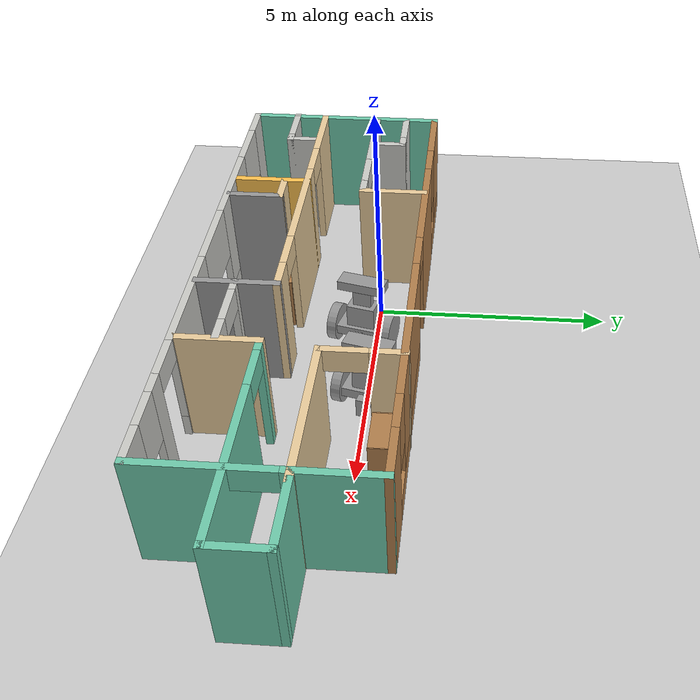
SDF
<sdf version="1.6">
 <world name="default">
  <plugin name="welcome_message" filename="libhello.so"/>
  <light name="sun" type="directional">
   <pose>0 0 10 0 -0 0</pose>
   <diffuse>0.8 0.8 0.8 1</diffuse>
   <specular>0.2 0.2 0.2 1</specular>
   <attenuation>
    <range>1000</range>
    <constant>0.9</constant>
    <linear>0.01</linear>
    <quadratic>0.001</quadratic>
   </attenuation>
   <direction>-0.5 0.1 -0.9</direction>
  </light>
  <model name="ground_plane">
   <static>1</static>
   <link name="link">
    <collision name="collision">
     <geometry><plane><normal>0 0 1</normal><size>100 100</size></plane></geometry>
     <surface>
      <contact><collide_bitmask>65535</collide_bitmask></contact>
      <friction><ode><mu>100</mu><mu2>50</mu2></ode></friction>
     </surface>
    </collision>
    <visual name="visual">
     <cast_shadows>0</cast_shadows>
     <geometry><plane><normal>0 0 1</normal><size>100 100</size></plane></geometry>
     <material>
      <script><uri>file://media/materials/scripts/gazebo.material</uri><name>Gazebo/Grey</name></script>
     </material>
    </visual>
   </link>
  </model>
  <gravity>0 0 -9.8</gravity>
  <magnetic_field>6e-06 2.3e-05 -4.2e-05</magnetic_field>
  <atmosphere type="adiabatic"/>
  <physics name="default_physics" default="0" type="ode">
   <max_step_size>0.001</max_step_size>
   <real_time_factor>1</real_time_factor>
   <real_time_update_rate>1000</real_time_update_rate>
  </physics>
  <scene><ambient>0.4 0.4 0.4 1</ambient><background>0.7 0.7 0.7 1</background><shadows>1</shadows></scene>
  <spherical_coordinates>
   <surface_model>EARTH_WGS84</surface_model>
   <latitude_deg>0</latitude_deg>
   <longitude_deg>0</longitude_deg>
   <elevation>0</elevation>
   <heading_deg>0</heading_deg>
  </spherical_coordinates>
  <model name="world">
   <pose>2.0565 -1.24663 0 0 -0 0</pose>
   <link name="Wall_1">
    <collision name="Wall_1_Collision">
     <geometry><box><size>4.5 0.15 2.5</size></box></geometry>
     <pose>0 0 1.25 0 -0 0</pose>
    </collision>
    <visual name="Wall_1_Visual">
     <pose>0 0 1.25 0 -0 0</pose>
     <geometry><box><size>4.5 0.15 2.5</size></box></geometry>
     <material>
      <script><uri>file://media/materials/scripts/gazebo.material</uri><name>Gazebo/Grey</name></script>
      <ambient>0.435294 0.796078 0.67451 1</ambient>
     </material>
     <meta><layer>0</layer></meta>
    </visual>
    <pose>-6.42328 -0.007904 0 0 0 -1.5708</pose>
   </link>
   <link name="Wall_10">
    <pose>4.16351 -0.517095 0 0 -0 0</pose>
    <visual name="Wall_10_Visual_0">
     <pose>-2.20046 0 1.25 0 -0 0</pose>
     <geometry><box><size>0.349089 0.15 2.5</size></box></geometry>
     <material>
      <script><uri>file://media/materials/scripts/gazebo.material</uri><name>Gazebo/Grey</name></script>
      <ambient>0.435294 0.796078 0.67451 1</ambient>
     </material>
     <meta><layer>0</layer></meta>
    </visual>
    <collision name="Wall_10_Collision_0">
     <geometry><box><size>0.349089 0.15 2.5</size></box></geometry>
     <pose>-2.20046 0 1.25 0 -0 0</pose>
    </collision>
    <visual name="Wall_10_Visual_1">
     <pose>0.624544 0 1.25 0 -0 0</pose>
     <geometry><box><size>3.50091 0.15 2.5</size></box></geometry>
     <material>
      <script><uri>file://media/materials/scripts/gazebo.material</uri><name>Gazebo/Grey</name></script>
      <ambient>0.435294 0.796078 0.67451 1</ambient>
     </material>
     <meta><layer>0</layer></meta>
    </visual>
    <collision name="Wall_10_Collision_1">
     <geometry><box><size>3.50091 0.15 2.5</size></box></geometry>
     <pose>0.624544 0 1.25 0 -0 0</pose>
    </collision>
    <visual name="Wall_10_Visual_2">
     <pose>-1.57591 0 2.25 0 -0 0</pose>
     <geometry><box><size>0.9 0.15 0.5</size></box></geometry>
     <material>
      <script><uri>file://media/materials/scripts/gazebo.material</uri><name>Gazebo/Grey</name></script>
      <ambient>0.435294 0.796078 0.67451 1</ambient>
     </material>
     <meta><layer>0</layer></meta>
    </visual>
    <collision name="Wall_10_Collision_2">
     <geometry><box><size>0.9 0.15 0.5</size></box></geometry>
     <pose>-1.57591 0 2.25 0 -0 0</pose>
    </collision>
   </link>
   <link name="Wall_11">
    <collision name="Wall_11_Collision">
     <geometry><box><size>1.25 0.15 2.5</size></box></geometry>
     <pose>0 0 1.25 0 -0 0</pose>
    </collision>
    <visual name="Wall_11_Visual">
     <pose>0 0 1.25 0 -0 0</pose>
     <geometry><box><size>1.25 0.15 2.5</size></box></geometry>
     <material>
      <script><uri>file://media/materials/scripts/gazebo.material</uri><name>Gazebo/Grey</name></script>
      <ambient>0.435294 0.796078 0.67451 1</ambient>
     </material>
     <meta><layer>0</layer></meta>
    </visual>
    <pose>6.46351 0.032905 0 0 -0 1.5708</pose>
   </link>
   <link name="Wall_12">
    <collision name="Wall_12_Collision">
     <geometry><box><size>1.5 0.15 2.5</size></box></geometry>
     <pose>0 0 1.25 0 -0 0</pose>
    </collision>
    <visual name="Wall_12_Visual">
     <pose>0 0 1.25 0 -0 0</pose>
     <geometry><box><size>1.5 0.15 2.5</size></box></geometry>
     <material>
      <script><uri>file://media/materials/scripts/gazebo.material</uri><name>Gazebo/Grey</name></script>
      <ambient>0.435294 0.796078 0.67451 1</ambient>
     </material>
     <meta><layer>0</layer></meta>
    </visual>
    <pose>5.78851 0.582905 0 0 -0 3.14159</pose>
   </link>
   <link name="Wall_14">
    <collision name="Wall_14_Collision">
     <geometry><box><size>1.75 0.15 2.5</size></box></geometry>
     <pose>0 0 1.25 0 -0 0</pose>
    </collision>
    <visual name="Wall_14_Visual">
     <pose>0 0 1.25 0 -0 0</pose>
     <geometry><box><size>1.75 0.15 2.5</size></box></geometry>
     <material>
      <script><uri>file://media/materials/scripts/gazebo.material</uri><name>Gazebo/Grey</name></script>
      <ambient>1 0.764706 0.305882 1</ambient>
     </material>
     <meta><layer>0</layer></meta>
    </visual>
    <pose>-3.54704 -1.30801 0 0 0 -1.5708</pose>
   </link>
   <link name="Wall_16">
    <pose>-4.79283 0.779259 0 0 -0 0</pose>
    <visual name="Wall_16_Visual_0">
     <pose>-0.68614 0 1.25 0 -0 0</pose>
     <geometry><box><size>1.87772 0.15 2.5</size></box></geometry>
     <material>
      <script><uri>file://media/materials/scripts/gazebo.material</uri><name>Gazebo/CeilingTiled</name></script>
      <ambient>0.921569 0.807843 0.615686 1</ambient>
     </material>
     <meta><layer>0</layer></meta>
    </visual>
    <collision name="Wall_16_Collision_0">
     <geometry><box><size>1.87772 0.15 2.5</size></box></geometry>
     <pose>-0.68614 0 1.25 0 -0 0</pose>
    </collision>
    <visual name="Wall_16_Visual_1">
     <pose>1.38886 0 1.25 0 -0 0</pose>
     <geometry><box><size>0.47228 0.15 2.5</size></box></geometry>
     <material>
      <script><uri>file://media/materials/scripts/gazebo.material</uri><name>Gazebo/CeilingTiled</name></script>
      <ambient>0.921569 0.807843 0.615686 1</ambient>
     </material>
     <meta><layer>0</layer></meta>
    </visual>
    <collision name="Wall_16_Collision_1">
     <geometry><box><size>0.47228 0.15 2.5</size></box></geometry>
     <pose>1.38886 0 1.25 0 -0 0</pose>
    </collision>
    <visual name="Wall_16_Visual_2">
     <pose>0.70272 0 2.25 0 -0 0</pose>
     <geometry><box><size>0.9 0.15 0.5</size></box></geometry>
     <material>
      <script><uri>file://media/materials/scripts/gazebo.material</uri><name>Gazebo/CeilingTiled</name></script>
      <ambient>0.921569 0.807843 0.615686 1</ambient>
     </material>
     <meta><layer>0</layer></meta>
    </visual>
    <collision name="Wall_16_Collision_2">
     <geometry><box><size>0.9 0.15 0.5</size></box></geometry>
     <pose>0.70272 0 2.25 0 -0 0</pose>
    </collision>
   </link>
   <link name="Wall_17">
    <collision name="Wall_17_Collision">
     <geometry><box><size>1.5 0.15 2.5</size></box></geometry>
     <pose>0 0 1.25 0 -0 0</pose>
    </collision>
    <visual name="Wall_17_Visual">
     <pose>0 0 1.25 0 -0 0</pose>
     <geometry><box><size>1.5 0.15 2.5</size></box></geometry>
     <material>
      <script><uri>file://media/materials/scripts/gazebo.material</uri><name>Gazebo/Grey</name></script>
      <ambient>0.921569 0.807843 0.615686 1</ambient>
     </material>
     <meta><layer>0</layer></meta>
    </visual>
    <pose>-3.24283 1.45426 0 0 -0 1.5708</pose>
   </link>
   <link name="Wall_2">
    <pose>-0.748282 -2.1829 0 0 -0 0</pose>
    <visual name="Wall_2_Visual_0">
     <pose>-5.32921 0 1.25 0 -0 0</pose>
     <geometry><box><size>0.841587 0.15 2.5</size></box></geometry>
     <material>
      <script><uri>file://media/materials/scripts/gazebo.material</uri><name>Gazebo/CeilingTiled</name></script>
      <ambient>0.435294 0.796078 0.67451 1</ambient>
     </material>
     <meta><layer>0</layer></meta>
    </visual>
    <collision name="Wall_2_Collision_0">
     <geometry><box><size>0.841587 0.15 2.5</size></box></geometry>
     <pose>-5.32921 0 1.25 0 -0 0</pose>
    </collision>
    <visual name="Wall_2_Visual_1">
     <pose>3.85366 0 1.25 0 -0 0</pose>
     <geometry><box><size>0.457382 0.15 2.5</size></box></geometry>
     <material>
      <script><uri>file://media/materials/scripts/gazebo.material</uri><name>Gazebo/CeilingTiled</name></script>
      <ambient>0.435294 0.796078 0.67451 1</ambient>
     </material>
     <meta><layer>0</layer></meta>
    </visual>
    <collision name="Wall_2_Collision_1">
     <geometry><box><size>0.457382 0.15 2.5</size></box></geometry>
     <pose>3.85366 0 1.25 0 -0 0</pose>
    </collision>
    <visual name="Wall_2_Visual_2">
     <pose>-1.09172 0 0.25 0 -0 0</pose>
     <geometry><box><size>7.63338 0.15 0.5</size></box></geometry>
     <material>
      <script><uri>file://media/materials/scripts/gazebo.material</uri><name>Gazebo/CeilingTiled</name></script>
      <ambient>0.435294 0.796078 0.67451 1</ambient>
     </material>
     <meta><layer>0</layer></meta>
    </visual>
    <collision name="Wall_2_Collision_2">
     <geometry><box><size>7.63338 0.15 0.5</size></box></geometry>
     <pose>-1.09172 0 0.25 0 -0 0</pose>
    </collision>
    <visual name="Wall_2_Visual_3">
     <pose>4.91618 0 0.25 0 -0 0</pose>
     <geometry><box><size>1.66765 0.15 0.5</size></box></geometry>
     <material>
      <script><uri>file://media/materials/scripts/gazebo.material</uri><name>Gazebo/CeilingTiled</name></script>
      <ambient>0.435294 0.796078 0.67451 1</ambient>
     </material>
     <meta><layer>0</layer></meta>
    </visual>
    <collision name="Wall_2_Collision_3">
     <geometry><box><size>1.66765 0.15 0.5</size></box></geometry>
     <pose>4.91618 0 0.25 0 -0 0</pose>
    </collision>
    <visual name="Wall_2_Visual_4">
     <pose>-2.58757 0 1.5 0 -0 0</pose>
     <geometry><box><size>2.19692 0.15 2</size></box></geometry>
     <material>
      <script><uri>file://media/materials/scripts/gazebo.material</uri><name>Gazebo/CeilingTiled</name></script>
      <ambient>0.435294 0.796078 0.67451 1</ambient>
     </material>
     <meta><layer>0</layer></meta>
    </visual>
    <collision name="Wall_2_Collision_4">
     <geometry><box><size>2.19692 0.15 2</size></box></geometry>
     <pose>-2.58757 0 1.5 0 -0 0</pose>
    </collision>
    <visual name="Wall_2_Visual_5">
     <pose>1.45037 0 1.5 0 -0 0</pose>
     <geometry><box><size>2.54919 0.15 2</size></box></geometry>
     <material>
      <script><uri>file://media/materials/scripts/gazebo.material</uri><name>Gazebo/CeilingTiled</name></script>
      <ambient>0.435294 0.796078 0.67451 1</ambient>
     </material>
     <meta><layer>0</layer></meta>
    </visual>
    <collision name="Wall_2_Collision_5">
     <geometry><box><size>2.54919 0.15 2</size></box></geometry>
     <pose>1.45037 0 1.5 0 -0 0</pose>
    </collision>
    <visual name="Wall_2_Visual_6">
     <pose>1.45037 0 1.5 0 -0 0</pose>
     <geometry><box><size>2.54919 0.15 2</size></box></geometry>
     <material>
      <script><uri>file://media/materials/scripts/gazebo.material</uri><name>Gazebo/CeilingTiled</name></script>
      <ambient>0.435294 0.796078 0.67451 1</ambient>
     </material>
     <meta><layer>0</layer></meta>
    </visual>
    <collision name="Wall_2_Collision_6">
     <geometry><box><size>2.54919 0.15 2</size></box></geometry>
     <pose>1.45037 0 1.5 0 -0 0</pose>
    </collision>
    <visual name="Wall_2_Visual_7">
     <pose>5.31618 0 1.5 0 -0 0</pose>
     <geometry><box><size>0.867646 0.15 2</size></box></geometry>
     <material>
      <script><uri>file://media/materials/scripts/gazebo.material</uri><name>Gazebo/CeilingTiled</name></script>
      <ambient>0.435294 0.796078 0.67451 1</ambient>
     </material>
     <meta><layer>0</layer></meta>
    </visual>
    <collision name="Wall_2_Collision_7">
     <geometry><box><size>0.867646 0.15 2</size></box></geometry>
     <pose>5.31618 0 1.5 0 -0 0</pose>
    </collision>
    <visual name="Wall_2_Visual_8">
     <pose>-4.29722 0 1.9 0 -0 0</pose>
     <geometry><box><size>1.22239 0.15 1.2</size></box></geometry>
     <material>
      <script><uri>file://media/materials/scripts/gazebo.material</uri><name>Gazebo/CeilingTiled</name></script>
      <ambient>0.435294 0.796078 0.67451 1</ambient>
     </material>
     <meta><layer>0</layer></meta>
    </visual>
    <collision name="Wall_2_Collision_8">
     <geometry><box><size>1.22239 0.15 1.2</size></box></geometry>
     <pose>-4.29722 0 1.9 0 -0 0</pose>
    </collision>
    <visual name="Wall_2_Visual_9">
     <pose>4.48235 0 1.9 0 -0 0</pose>
     <geometry><box><size>0.8 0.15 1.2</size></box></geometry>
     <material>
      <script><uri>file://media/materials/scripts/gazebo.material</uri><name>Gazebo/CeilingTiled</name></script>
      <ambient>0.435294 0.796078 0.67451 1</ambient>
     </material>
     <meta><layer>0</layer></meta>
    </visual>
    <collision name="Wall_2_Collision_9">
     <geometry><box><size>0.8 0.15 1.2</size></box></geometry>
     <pose>4.48235 0 1.9 0 -0 0</pose>
    </collision>
    <visual name="Wall_2_Visual_10">
     <pose>-0.656664 0 1.9 0 -0 0</pose>
     <geometry><box><size>1.66488 0.15 1.2</size></box></geometry>
     <material>
      <script><uri>file://media/materials/scripts/gazebo.material</uri><name>Gazebo/CeilingTiled</name></script>
      <ambient>0.435294 0.796078 0.67451 1</ambient>
     </material>
     <meta><layer>0</layer></meta>
    </visual>
    <collision name="Wall_2_Collision_10">
     <geometry><box><size>1.66488 0.15 1.2</size></box></geometry>
     <pose>-0.656664 0 1.9 0 -0 0</pose>
    </collision>
    <visual name="Wall_2_Visual_11">
     <pose>3.17497 0 2.25 0 -0 0</pose>
     <geometry><box><size>0.9 0.15 0.5</size></box></geometry>
     <material>
      <script><uri>file://media/materials/scripts/gazebo.material</uri><name>Gazebo/CeilingTiled</name></script>
      <ambient>0.435294 0.796078 0.67451 1</ambient>
     </material>
     <meta><layer>0</layer></meta>
    </visual>
    <collision name="Wall_2_Collision_11">
     <geometry><box><size>0.9 0.15 0.5</size></box></geometry>
     <pose>3.17497 0 2.25 0 -0 0</pose>
    </collision>
    <visual name="Wall_2_Visual_12">
     <pose>3.17497 0 2.25 0 -0 0</pose>
     <geometry><box><size>0.9 0.15 0.5</size></box></geometry>
     <material>
      <script><uri>file://media/materials/scripts/gazebo.material</uri><name>Gazebo/CeilingTiled</name></script>
      <ambient>0.435294 0.796078 0.67451 1</ambient>
     </material>
     <meta><layer>0</layer></meta>
    </visual>
    <collision name="Wall_2_Collision_12">
     <geometry><box><size>0.9 0.15 0.5</size></box></geometry>
     <pose>3.17497 0 2.25 0 -0 0</pose>
    </collision>
   </link>
   <link name="Wall_21">
    <collision name="Wall_21_Collision">
     <geometry><box><size>3.25 0.15 2.5</size></box></geometry>
     <pose>0 0 1.25 0 -0 0</pose>
    </collision>
    <visual name="Wall_21_Visual">
     <pose>0 0 1.25 0 -0 0</pose>
     <geometry><box><size>3.25 0.15 2.5</size></box></geometry>
     <material>
      <script><uri>file://media/materials/scripts/gazebo.material</uri><name>Gazebo/Grey</name></script>
      <ambient>0.921569 0.807843 0.615686 1</ambient>
     </material>
     <meta><layer>0</layer></meta>
    </visual>
    <pose>3.56351 0.582905 0 0 -0 3.14159</pose>
   </link>
   <link name="Wall_22">
    <pose>2.01351 1.38291 0 0 -0 1.5708</pose>
    <visual name="Wall_22_Visual_0">
     <pose>-0.823528 0 1.25 0 -0 0</pose>
     <geometry><box><size>0.102944 0.15 2.5</size></box></geometry>
     <material>
      <script><uri>file://media/materials/scripts/gazebo.material</uri><name>Gazebo/Grey</name></script>
      <ambient>0.921569 0.807843 0.615686 1</ambient>
     </material>
     <meta><layer>0</layer></meta>
    </visual>
    <collision name="Wall_22_Collision_0">
     <geometry><box><size>0.102944 0.15 2.5</size></box></geometry>
     <pose>-0.823528 0 1.25 0 -0 0</pose>
    </collision>
    <visual name="Wall_22_Visual_1">
     <pose>0.501472 0 1.25 0 -0 0</pose>
     <geometry><box><size>0.747056 0.15 2.5</size></box></geometry>
     <material>
      <script><uri>file://media/materials/scripts/gazebo.material</uri><name>Gazebo/Grey</name></script>
      <ambient>0.921569 0.807843 0.615686 1</ambient>
     </material>
     <meta><layer>0</layer></meta>
    </visual>
    <collision name="Wall_22_Collision_1">
     <geometry><box><size>0.747056 0.15 2.5</size></box></geometry>
     <pose>0.501472 0 1.25 0 -0 0</pose>
    </collision>
    <visual name="Wall_22_Visual_2">
     <pose>-0.322056 0 2.25 0 -0 0</pose>
     <geometry><box><size>0.9 0.15 0.5</size></box></geometry>
     <material>
      <script><uri>file://media/materials/scripts/gazebo.material</uri><name>Gazebo/Grey</name></script>
      <ambient>0.921569 0.807843 0.615686 1</ambient>
     </material>
     <meta><layer>0</layer></meta>
    </visual>
    <collision name="Wall_22_Collision_2">
     <geometry><box><size>0.9 0.15 0.5</size></box></geometry>
     <pose>-0.322056 0 2.25 0 -0 0</pose>
    </collision>
   </link>
   <link name="Wall_24">
    <pose>-5.81294 1.48323 0 0 -0 0</pose>
    <visual name="Wall_24_Visual_0">
     <pose>0 0 1.25 0 -0 0</pose>
     <geometry><box><size>1.25 0.15 2.5</size></box></geometry>
     <material>
      <script><uri>file://media/materials/scripts/gazebo.material</uri><name>Gazebo/CeilingTiled</name></script>
      <ambient>0.921569 0.807843 0.615686 1</ambient>
     </material>
     <meta><layer>0</layer></meta>
    </visual>
    <collision name="Wall_24_Collision_0">
     <geometry><box><size>1.25 0.15 2.5</size></box></geometry>
     <pose>0 0 1.25 0 -0 0</pose>
    </collision>
    <visual name="Wall_24_Visual_1">
     <pose>0.433465 0 1.25 0 -0 0</pose>
     <geometry><box><size>0.383069 0.15 2.5</size></box></geometry>
     <material>
      <script><uri>file://media/materials/scripts/gazebo.material</uri><name>Gazebo/CeilingTiled</name></script>
      <ambient>0.921569 0.807843 0.615686 1</ambient>
     </material>
     <meta><layer>0</layer></meta>
    </visual>
    <collision name="Wall_24_Collision_1">
     <geometry><box><size>0.383069 0.15 2.5</size></box></geometry>
     <pose>0.433465 0 1.25 0 -0 0</pose>
    </collision>
   </link>
   <link name="Wall_27">
    <collision name="Wall_27_Collision">
     <geometry><box><size>0.75 0.15 2.5</size></box></geometry>
     <pose>0 0 1.25 0 -0 0</pose>
    </collision>
    <visual name="Wall_27_Visual">
     <pose>0 0 1.25 0 -0 0</pose>
     <geometry><box><size>0.75 0.15 2.5</size></box></geometry>
     <material>
      <script><uri>file://media/materials/scripts/gazebo.material</uri><name>Gazebo/CeilingTiled</name></script>
      <ambient>0.921569 0.807843 0.615686 1</ambient>
     </material>
     <meta><layer>0</layer></meta>
    </visual>
    <pose>-5.26294 1.18323 0 0 0 -1.5708</pose>
   </link>
   <link name="Wall_29">
    <pose>-5.91351 -1.19187 0 0 -0 0</pose>
    <visual name="Wall_29_Visual_0">
     <pose>-0.581194 0 1.25 0 -0 0</pose>
     <geometry><box><size>0.087612 0.15 2.5</size></box></geometry>
     <material>
      <script><uri>file://media/materials/scripts/gazebo.material</uri><name>Gazebo/CeilingTiled</name></script>
      <ambient>1 1 1 1</ambient>
     </material>
     <meta><layer>0</layer></meta>
    </visual>
    <collision name="Wall_29_Collision_0">
     <geometry><box><size>0.087612 0.15 2.5</size></box></geometry>
     <pose>-0.581194 0 1.25 0 -0 0</pose>
    </collision>
    <visual name="Wall_29_Visual_1">
     <pose>0.493806 0 1.25 0 -0 0</pose>
     <geometry><box><size>0.262388 0.15 2.5</size></box></geometry>
     <material>
      <script><uri>file://media/materials/scripts/gazebo.material</uri><name>Gazebo/CeilingTiled</name></script>
      <ambient>1 1 1 1</ambient>
     </material>
     <meta><layer>0</layer></meta>
    </visual>
    <collision name="Wall_29_Collision_1">
     <geometry><box><size>0.262388 0.15 2.5</size></box></geometry>
     <pose>0.493806 0 1.25 0 -0 0</pose>
    </collision>
    <visual name="Wall_29_Visual_2">
     <pose>-0.087388 0 2.25 0 -0 0</pose>
     <geometry><box><size>0.9 0.15 0.5</size></box></geometry>
     <material>
      <script><uri>file://media/materials/scripts/gazebo.material</uri><name>Gazebo/CeilingTiled</name></script>
      <ambient>1 1 1 1</ambient>
     </material>
     <meta><layer>0</layer></meta>
    </visual>
    <collision name="Wall_29_Collision_2">
     <geometry><box><size>0.9 0.15 0.5</size></box></geometry>
     <pose>-0.087388 0 2.25 0 -0 0</pose>
    </collision>
   </link>
   <link name="Wall_3">
    <pose>4.92672 -0.007904 0 0 -0 1.5708</pose>
    <visual name="Wall_3_Visual_0">
     <pose>-1.36875 0 1.25 0 -0 0</pose>
     <geometry><box><size>1.76251 0.15 2.5</size></box></geometry>
     <material>
      <script><uri>file://media/materials/scripts/gazebo.material</uri><name>Gazebo/Grey</name></script>
      <ambient>0.435294 0.796078 0.67451 1</ambient>
     </material>
     <meta><layer>0</layer></meta>
    </visual>
    <collision name="Wall_3_Collision_0">
     <geometry><box><size>1.76251 0.15 2.5</size></box></geometry>
     <pose>-1.36875 0 1.25 0 -0 0</pose>
    </collision>
    <visual name="Wall_3_Visual_1">
     <pose>1.33125 0 1.25 0 -0 0</pose>
     <geometry><box><size>1.83749 0.15 2.5</size></box></geometry>
     <material>
      <script><uri>file://media/materials/scripts/gazebo.material</uri><name>Gazebo/Grey</name></script>
      <ambient>0.435294 0.796078 0.67451 1</ambient>
     </material>
     <meta><layer>0</layer></meta>
    </visual>
    <collision name="Wall_3_Collision_1">
     <geometry><box><size>1.83749 0.15 2.5</size></box></geometry>
     <pose>1.33125 0 1.25 0 -0 0</pose>
    </collision>
    <visual name="Wall_3_Visual_2">
     <pose>-0.037493 0 2.25 0 -0 0</pose>
     <geometry><box><size>0.9 0.15 0.5</size></box></geometry>
     <material>
      <script><uri>file://media/materials/scripts/gazebo.material</uri><name>Gazebo/Grey</name></script>
      <ambient>0.435294 0.796078 0.67451 1</ambient>
     </material>
     <meta><layer>0</layer></meta>
    </visual>
    <collision name="Wall_3_Collision_2">
     <geometry><box><size>0.9 0.15 0.5</size></box></geometry>
     <pose>-0.037493 0 2.25 0 -0 0</pose>
    </collision>
   </link>
   <link name="Wall_30">
    <collision name="Wall_30_Collision">
     <geometry><box><size>0.75 0.15 2.5</size></box></geometry>
     <pose>0 0 1.25 0 -0 0</pose>
    </collision>
    <visual name="Wall_30_Visual">
     <pose>0 0 1.25 0 -0 0</pose>
     <geometry><box><size>0.75 0.15 2.5</size></box></geometry>
     <material>
      <script><uri>file://media/materials/scripts/gazebo.material</uri><name>Gazebo/CeilingTiled</name></script>
      <ambient>1 1 1 1</ambient>
     </material>
     <meta><layer>0</layer></meta>
    </visual>
    <pose>-5.36351 -0.891871 0 0 -0 1.5708</pose>
   </link>
   <link name="Wall_32">
    <collision name="Wall_32_Collision">
     <geometry><box><size>0.75 0.15 2.5</size></box></geometry>
     <pose>0 0 1.25 0 -0 0</pose>
    </collision>
    <visual name="Wall_32_Visual">
     <pose>0 0 1.25 0 -0 0</pose>
     <geometry><box><size>0.75 0.15 2.5</size></box></geometry>
     <material>
      <script><uri>file://media/materials/scripts/gazebo.material</uri><name>Gazebo/Grey</name></script>
      <ambient>0.921569 0.807843 0.615686 1</ambient>
     </material>
     <meta><layer>0</layer></meta>
    </visual>
    <pose>-3.20682 -1.01085 0 0 -0 0</pose>
   </link>
   <link name="Wall_33">
    <collision name="Wall_33_Collision">
     <geometry><box><size>1.25 0.15 2.5</size></box></geometry>
     <pose>0 0 1.25 0 -0 0</pose>
    </collision>
    <visual name="Wall_33_Visual">
     <pose>0 0 1.25 0 -0 0</pose>
     <geometry><box><size>1.25 0.15 2.5</size></box></geometry>
     <material>
      <script><uri>file://media/materials/scripts/gazebo.material</uri><name>Gazebo/Grey</name></script>
      <ambient>1 1 1 1</ambient>
     </material>
     <meta><layer>0</layer></meta>
    </visual>
    <pose>-2.90681 -1.56085 0 0 0 -1.5708</pose>
   </link>
   <link name="Wall_35">
    <pose>0.994083 -1.35278 0 0 -0 0</pose>
    <visual name="Wall_35_Visual_0">
     <pose>-0.720569 0 1.25 0 -0 0</pose>
     <geometry><box><size>0.308861 0.15 2.5</size></box></geometry>
     <material>
      <script><uri>file://media/materials/scripts/gazebo.material</uri><name>Gazebo/CeilingTiled</name></script>
      <ambient>0.921569 0.807843 0.615686 1</ambient>
     </material>
     <meta><layer>0</layer></meta>
    </visual>
    <collision name="Wall_35_Collision_0">
     <geometry><box><size>0.308861 0.15 2.5</size></box></geometry>
     <pose>-0.720569 0 1.25 0 -0 0</pose>
    </collision>
    <visual name="Wall_35_Visual_1">
     <pose>0.604431 0 1.25 0 -0 0</pose>
     <geometry><box><size>0.541139 0.15 2.5</size></box></geometry>
     <material>
      <script><uri>file://media/materials/scripts/gazebo.material</uri><name>Gazebo/CeilingTiled</name></script>
      <ambient>0.921569 0.807843 0.615686 1</ambient>
     </material>
     <meta><layer>0</layer></meta>
    </visual>
    <collision name="Wall_35_Collision_1">
     <geometry><box><size>0.541139 0.15 2.5</size></box></geometry>
     <pose>0.604431 0 1.25 0 -0 0</pose>
    </collision>
    <visual name="Wall_35_Visual_2">
     <pose>-0.116139 0 2.25 0 -0 0</pose>
     <geometry><box><size>0.9 0.15 0.5</size></box></geometry>
     <material>
      <script><uri>file://media/materials/scripts/gazebo.material</uri><name>Gazebo/CeilingTiled</name></script>
      <ambient>0.921569 0.807843 0.615686 1</ambient>
     </material>
     <meta><layer>0</layer></meta>
    </visual>
    <collision name="Wall_35_Collision_2">
     <geometry><box><size>0.9 0.15 0.5</size></box></geometry>
     <pose>-0.116139 0 2.25 0 -0 0</pose>
    </collision>
   </link>
   <link name="Wall_4">
    <pose>-0.748282 2.1671 0 0 -0 3.14159</pose>
    <visual name="Wall_4_Visual_0">
     <pose>-5.18544 0 1.25 0 -0 0</pose>
     <geometry><box><size>1.12912 0.15 2.5</size></box></geometry>
     <material>
      <script><uri>file://media/materials/scripts/gazebo.material</uri><name>Gazebo/Wood</name></script>
      <ambient>0.435294 0.796078 0.67451 1</ambient>
     </material>
     <meta><layer>0</layer></meta>
    </visual>
    <collision name="Wall_4_Collision_0">
     <geometry><box><size>1.12912 0.15 2.5</size></box></geometry>
     <pose>-5.18544 0 1.25 0 -0 0</pose>
    </collision>
    <visual name="Wall_4_Visual_1">
     <pose>2.12984 0 1.25 0 -0 0</pose>
     <geometry><box><size>2.66988 0.15 2.5</size></box></geometry>
     <material>
      <script><uri>file://media/materials/scripts/gazebo.material</uri><name>Gazebo/Wood</name></script>
      <ambient>0.435294 0.796078 0.67451 1</ambient>
     </material>
     <meta><layer>0</layer></meta>
    </visual>
    <collision name="Wall_4_Collision_1">
     <geometry><box><size>2.66988 0.15 2.5</size></box></geometry>
     <pose>2.12984 0 1.25 0 -0 0</pose>
    </collision>
    <visual name="Wall_4_Visual_2">
     <pose>-2.36299 0 0.25 0 -0 0</pose>
     <geometry><box><size>4.51578 0.15 0.5</size></box></geometry>
     <material>
      <script><uri>file://media/materials/scripts/gazebo.material</uri><name>Gazebo/Wood</name></script>
      <ambient>0.435294 0.796078 0.67451 1</ambient>
     </material>
     <meta><layer>0</layer></meta>
    </visual>
    <collision name="Wall_4_Collision_2">
     <geometry><box><size>4.51578 0.15 0.5</size></box></geometry>
     <pose>-2.36299 0 0.25 0 -0 0</pose>
    </collision>
    <visual name="Wall_4_Visual_3">
     <pose>4.60739 0 0.25 0 -0 0</pose>
     <geometry><box><size>2.28522 0.15 0.5</size></box></geometry>
     <material>
      <script><uri>file://media/materials/scripts/gazebo.material</uri><name>Gazebo/Wood</name></script>
      <ambient>0.435294 0.796078 0.67451 1</ambient>
     </material>
     <meta><layer>0</layer></meta>
    </visual>
    <collision name="Wall_4_Collision_3">
     <geometry><box><size>2.28522 0.15 0.5</size></box></geometry>
     <pose>4.60739 0 0.25 0 -0 0</pose>
    </collision>
    <visual name="Wall_4_Visual_4">
     <pose>-1.96299 0 1.5 0 -0 0</pose>
     <geometry><box><size>3.71578 0.15 2</size></box></geometry>
     <material>
      <script><uri>file://media/materials/scripts/gazebo.material</uri><name>Gazebo/Wood</name></script>
      <ambient>0.435294 0.796078 0.67451 1</ambient>
     </material>
     <meta><layer>0</layer></meta>
    </visual>
    <collision name="Wall_4_Collision_4">
     <geometry><box><size>3.71578 0.15 2</size></box></geometry>
     <pose>-1.96299 0 1.5 0 -0 0</pose>
    </collision>
    <visual name="Wall_4_Visual_5">
     <pose>-1.96299 0 1.5 0 -0 0</pose>
     <geometry><box><size>3.71578 0.15 2</size></box></geometry>
     <material>
      <script><uri>file://media/materials/scripts/gazebo.material</uri><name>Gazebo/Wood</name></script>
      <ambient>0.435294 0.796078 0.67451 1</ambient>
     </material>
     <meta><layer>0</layer></meta>
    </visual>
    <collision name="Wall_4_Collision_5">
     <geometry><box><size>3.71578 0.15 2</size></box></geometry>
     <pose>-1.96299 0 1.5 0 -0 0</pose>
    </collision>
    <visual name="Wall_4_Visual_6">
     <pose>5.00739 0 1.5 0 -0 0</pose>
     <geometry><box><size>1.48522 0.15 2</size></box></geometry>
     <material>
      <script><uri>file://media/materials/scripts/gazebo.material</uri><name>Gazebo/Wood</name></script>
      <ambient>0.435294 0.796078 0.67451 1</ambient>
     </material>
     <meta><layer>0</layer></meta>
    </visual>
    <collision name="Wall_4_Collision_6">
     <geometry><box><size>1.48522 0.15 2</size></box></geometry>
     <pose>5.00739 0 1.5 0 -0 0</pose>
    </collision>
    <visual name="Wall_4_Visual_7">
     <pose>-4.22088 0 1.9 0 -0 0</pose>
     <geometry><box><size>0.8 0.15 1.2</size></box></geometry>
     <material>
      <script><uri>file://media/materials/scripts/gazebo.material</uri><name>Gazebo/Wood</name></script>
      <ambient>0.435294 0.796078 0.67451 1</ambient>
     </material>
     <meta><layer>0</layer></meta>
    </visual>
    <collision name="Wall_4_Collision_7">
     <geometry><box><size>0.8 0.15 1.2</size></box></geometry>
     <pose>-4.22088 0 1.9 0 -0 0</pose>
    </collision>
    <visual name="Wall_4_Visual_8">
     <pose>3.86478 0 1.9 0 -0 0</pose>
     <geometry><box><size>0.8 0.15 1.2</size></box></geometry>
     <material>
      <script><uri>file://media/materials/scripts/gazebo.material</uri><name>Gazebo/Wood</name></script>
      <ambient>0.435294 0.796078 0.67451 1</ambient>
     </material>
     <meta><layer>0</layer></meta>
    </visual>
    <collision name="Wall_4_Collision_8">
     <geometry><box><size>0.8 0.15 1.2</size></box></geometry>
     <pose>3.86478 0 1.9 0 -0 0</pose>
    </collision>
    <visual name="Wall_4_Visual_9">
     <pose>0.344903 0 2.25 0 -0 0</pose>
     <geometry><box><size>0.9 0.15 0.5</size></box></geometry>
     <material>
      <script><uri>file://media/materials/scripts/gazebo.material</uri><name>Gazebo/Wood</name></script>
      <ambient>0.435294 0.796078 0.67451 1</ambient>
     </material>
     <meta><layer>0</layer></meta>
    </visual>
    <collision name="Wall_4_Collision_9">
     <geometry><box><size>0.9 0.15 0.5</size></box></geometry>
     <pose>0.344903 0 2.25 0 -0 0</pose>
    </collision>
    <visual name="Wall_4_Visual_10">
     <pose>0.344903 0 2.25 0 -0 0</pose>
     <geometry><box><size>0.9 0.15 0.5</size></box></geometry>
     <material>
      <script><uri>file://media/materials/scripts/gazebo.material</uri><name>Gazebo/Wood</name></script>
      <ambient>0.435294 0.796078 0.67451 1</ambient>
     </material>
     <meta><layer>0</layer></meta>
    </visual>
    <collision name="Wall_4_Collision_10">
     <geometry><box><size>0.9 0.15 0.5</size></box></geometry>
     <pose>0.344903 0 2.25 0 -0 0</pose>
    </collision>
   </link>
   <link name="Wall_6">
    <pose>-3.12328 -0.50801 0 0 -0 0</pose>
    <visual name="Wall_6_Visual_0">
     <pose>-2.58699 0 1.25 0 -0 0</pose>
     <geometry><box><size>1.57602 0.15 2.5</size></box></geometry>
     <material>
      <script><uri>file://media/materials/scripts/gazebo.material</uri><name>Gazebo/Grey</name></script>
      <ambient>0.921569 0.807843 0.615686 1</ambient>
     </material>
     <meta><layer>0</layer></meta>
    </visual>
    <collision name="Wall_6_Collision_0">
     <geometry><box><size>1.57602 0.15 2.5</size></box></geometry>
     <pose>-2.58699 0 1.25 0 -0 0</pose>
    </collision>
    <visual name="Wall_6_Visual_1">
     <pose>0.410954 0 1.25 0 -0 0</pose>
     <geometry><box><size>2.61987 0.15 2.5</size></box></geometry>
     <material>
      <script><uri>file://media/materials/scripts/gazebo.material</uri><name>Gazebo/Grey</name></script>
      <ambient>0.921569 0.807843 0.615686 1</ambient>
     </material>
     <meta><layer>0</layer></meta>
    </visual>
    <collision name="Wall_6_Collision_1">
     <geometry><box><size>2.61987 0.15 2.5</size></box></geometry>
     <pose>0.410954 0 1.25 0 -0 0</pose>
    </collision>
    <visual name="Wall_6_Visual_2">
     <pose>2.99795 0 1.25 0 -0 0</pose>
     <geometry><box><size>0.754108 0.15 2.5</size></box></geometry>
     <material>
      <script><uri>file://media/materials/scripts/gazebo.material</uri><name>Gazebo/Grey</name></script>
      <ambient>0.921569 0.807843 0.615686 1</ambient>
     </material>
     <meta><layer>0</layer></meta>
    </visual>
    <collision name="Wall_6_Collision_2">
     <geometry><box><size>0.754108 0.15 2.5</size></box></geometry>
     <pose>2.99795 0 1.25 0 -0 0</pose>
    </collision>
    <visual name="Wall_6_Visual_3">
     <pose>-1.34898 0 2.25 0 -0 0</pose>
     <geometry><box><size>0.9 0.15 0.5</size></box></geometry>
     <material>
      <script><uri>file://media/materials/scripts/gazebo.material</uri><name>Gazebo/Grey</name></script>
      <ambient>0.921569 0.807843 0.615686 1</ambient>
     </material>
     <meta><layer>0</layer></meta>
    </visual>
    <collision name="Wall_6_Collision_3">
     <geometry><box><size>0.9 0.15 0.5</size></box></geometry>
     <pose>-1.34898 0 2.25 0 -0 0</pose>
    </collision>
    <visual name="Wall_6_Visual_4">
     <pose>2.17089 0 2.25 0 -0 0</pose>
     <geometry><box><size>0.9 0.15 0.5</size></box></geometry>
     <material>
      <script><uri>file://media/materials/scripts/gazebo.material</uri><name>Gazebo/Grey</name></script>
      <ambient>0.921569 0.807843 0.615686 1</ambient>
     </material>
     <meta><layer>0</layer></meta>
    </visual>
    <collision name="Wall_6_Collision_4">
     <geometry><box><size>0.9 0.15 0.5</size></box></geometry>
     <pose>2.17089 0 2.25 0 -0 0</pose>
    </collision>
   </link>
   <link name="Wall_7">
    <collision name="Wall_7_Collision">
     <geometry><box><size>1.75 0.15 2.5</size></box></geometry>
     <pose>0 0 1.25 0 -0 0</pose>
    </collision>
    <visual name="Wall_7_Visual">
     <pose>0 0 1.25 0 -0 0</pose>
     <geometry><box><size>1.75 0.15 2.5</size></box></geometry>
     <material>
      <script><uri>file://media/materials/scripts/gazebo.material</uri><name>Gazebo/Grey</name></script>
      <ambient>1 1 1 1</ambient>
     </material>
     <meta><layer>0</layer></meta>
    </visual>
    <pose>0.176718 -1.30801 0 0 0 -1.5708</pose>
   </link>
   <link name="Wall_9">
    <collision name="Wall_9_Collision">
     <geometry><box><size>1.75 0.15 2.5</size></box></geometry>
     <pose>0 0 1.25 0 -0 0</pose>
    </collision>
    <visual name="Wall_9_Visual">
     <pose>0 0 1.25 0 -0 0</pose>
     <geometry><box><size>1.75 0.15 2.5</size></box></geometry>
     <material>
      <script><uri>file://media/materials/scripts/gazebo.material</uri><name>Gazebo/Grey</name></script>
      <ambient>0.921569 0.807843 0.615686 1</ambient>
     </material>
     <meta><layer>0</layer></meta>
    </visual>
    <pose>1.86351 -1.31709 0 0 -0 1.5708</pose>
   </link>
   <static>1</static>
  </model>
  <model name="robo1">
   <link name="link_0">
    <pose>0.431648 -0.223766 0.4 0 -0 0</pose>
    <inertial>
     <mass>1</mass>
     <inertia>
      <ixx>0.166667</ixx>
      <ixy>0</ixy>
      <ixz>0</ixz>
      <iyy>0.166667</iyy>
      <iyz>0</iyz>
      <izz>0.166667</izz>
     </inertia>
    </inertial>
    <visual name="visual">
     <geometry><box><size>0.6 1 0.2</size></box></geometry>
     <material>
      <lighting>1</lighting>
      <script><uri>file://media/materials/scripts/gazebo.material</uri><name>Gazebo/Grey</name></script>
      <shader type="pixel"><normal_map>__default__</normal_map></shader>
      <ambient>0.3 0.3 0.3 1</ambient>
      <diffuse>0.7 0.7 0.7 1</diffuse>
      <specular>0.01 0.01 0.01 1</specular>
      <emissive>0 0 0 1</emissive>
     </material>
    </visual>
    <collision name="collision">
     <geometry><box><size>0.6 1 0.2</size></box></geometry>
     <surface>
      <friction>
       <ode><mu>1</mu><mu2>1</mu2><fdir1>0 0 0</fdir1><slip1>0</slip1><slip2>0</slip2></ode>
       <torsional>
        <coefficient>1</coefficient>
        <patch_radius>0</patch_radius>
        <surface_radius>0</surface_radius>
        <use_patch_radius>1</use_patch_radius>
        <ode><slip>0</slip></ode>
       </torsional>
      </friction>
      <bounce><restitution_coefficient>0</restitution_coefficient><threshold>1e+06</threshold></bounce>
      <contact>
       <collide_without_contact>0</collide_without_contact>
       <collide_without_contact_bitmask>1</collide_without_contact_bitmask>
       <collide_bitmask>1</collide_bitmask>
       <ode>
        <soft_cfm>0</soft_cfm>
        <soft_erp>0.2</soft_erp>
        <kp>1e+13</kp>
        <kd>1</kd>
        <max_vel>0.01</max_vel>
        <min_depth>0</min_depth>
       </ode>
       <bullet>
        <split_impulse>1</split_impulse>
        <split_impulse_penetration_threshold>-0.01</split_impulse_penetration_threshold>
        <soft_cfm>0</soft_cfm>
        <soft_erp>0.2</soft_erp>
        <kp>1e+13</kp>
        <kd>1</kd>
       </bullet>
      </contact>
     </surface>
    </collision>
   </link>
   <link name="link_10">
    <pose>0.431648 -0.223766 1.47714 0 -0 0</pose>
    <inertial>
     <mass>1</mass>
     <inertia>
      <ixx>0.166667</ixx>
      <ixy>0</ixy>
      <ixz>0</ixz>
      <iyy>0.166667</iyy>
      <iyz>0</iyz>
      <izz>0.166667</izz>
     </inertia>
    </inertial>
    <visual name="visual">
     <geometry><box><size>0.4 1 0.2</size></box></geometry>
     <material>
      <lighting>1</lighting>
      <script><uri>file://media/materials/scripts/gazebo.material</uri><name>Gazebo/Grey</name></script>
      <shader type="pixel"><normal_map>__default__</normal_map></shader>
      <ambient>0.3 0.3 0.3 1</ambient>
      <diffuse>0.7 0.7 0.7 1</diffuse>
      <specular>0.01 0.01 0.01 1</specular>
      <emissive>0 0 0 1</emissive>
     </material>
    </visual>
    <collision name="collision">
     <geometry><box><size>0.4 1 0.2</size></box></geometry>
     <surface>
      <friction>
       <ode><mu>1</mu><mu2>1</mu2><fdir1>0 0 0</fdir1><slip1>0</slip1><slip2>0</slip2></ode>
       <torsional>
        <coefficient>1</coefficient>
        <patch_radius>0</patch_radius>
        <surface_radius>0</surface_radius>
        <use_patch_radius>1</use_patch_radius>
        <ode><slip>0</slip></ode>
       </torsional>
      </friction>
      <bounce><restitution_coefficient>0</restitution_coefficient><threshold>1e+06</threshold></bounce>
      <contact>
       <collide_without_contact>0</collide_without_contact>
       <collide_without_contact_bitmask>1</collide_without_contact_bitmask>
       <collide_bitmask>1</collide_bitmask>
       <ode>
        <soft_cfm>0</soft_cfm>
        <soft_erp>0.2</soft_erp>
        <kp>1e+13</kp>
        <kd>1</kd>
        <max_vel>0.01</max_vel>
        <min_depth>0</min_depth>
       </ode>
       <bullet>
        <split_impulse>1</split_impulse>
        <split_impulse_penetration_threshold>-0.01</split_impulse_penetration_threshold>
        <soft_cfm>0</soft_cfm>
        <soft_erp>0.2</soft_erp>
        <kp>1e+13</kp>
        <kd>1</kd>
       </bullet>
      </contact>
     </surface>
    </collision>
   </link>
   <link name="link_2">
    <pose>0.431648 -0.823804 0.4 1.5707 -0 0</pose>
    <inertial>
     <mass>1</mass>
     <inertia><ixx>0.145833</ixx><ixy>0</ixy><ixz>0</ixz><iyy>0.145833</iyy><iyz>0</iyz><izz>0.125</izz></inertia>
    </inertial>
    <visual name="visual">
     <geometry><cylinder><radius>0.4</radius><length>0.2</length></cylinder></geometry>
     <material>
      <lighting>1</lighting>
      <script><uri>file://media/materials/scripts/gazebo.material</uri><name>Gazebo/Grey</name></script>
      <shader type="pixel"><normal_map>__default__</normal_map></shader>
      <ambient>0.3 0.3 0.3 1</ambient>
      <diffuse>0.7 0.7 0.7 1</diffuse>
      <specular>0.01 0.01 0.01 1</specular>
      <emissive>0 0 0 1</emissive>
     </material>
    </visual>
    <collision name="collision">
     <geometry><cylinder><radius>0.4</radius><length>0.2</length></cylinder></geometry>
     <surface>
      <friction>
       <ode><mu>1</mu><mu2>1</mu2><fdir1>0 0 0</fdir1><slip1>0</slip1><slip2>0</slip2></ode>
       <torsional>
        <coefficient>1</coefficient>
        <patch_radius>0</patch_radius>
        <surface_radius>0</surface_radius>
        <use_patch_radius>1</use_patch_radius>
        <ode><slip>0</slip></ode>
       </torsional>
      </friction>
      <bounce><restitution_coefficient>0</restitution_coefficient><threshold>1e+06</threshold></bounce>
      <contact>
       <collide_without_contact>0</collide_without_contact>
       <collide_without_contact_bitmask>1</collide_without_contact_bitmask>
       <collide_bitmask>1</collide_bitmask>
       <ode>
        <soft_cfm>0</soft_cfm>
        <soft_erp>0.2</soft_erp>
        <kp>1e+13</kp>
        <kd>1</kd>
        <max_vel>0.01</max_vel>
        <min_depth>0</min_depth>
       </ode>
       <bullet>
        <split_impulse>1</split_impulse>
        <split_impulse_penetration_threshold>-0.01</split_impulse_penetration_threshold>
        <soft_cfm>0</soft_cfm>
        <soft_erp>0.2</soft_erp>
        <kp>1e+13</kp>
        <kd>1</kd>
       </bullet>
      </contact>
     </surface>
    </collision>
   </link>
   <link name="link_2_clone">
    <pose>0.431648 0.376273 0.4 1.5707 -0 0</pose>
    <inertial>
     <mass>1</mass>
     <inertia><ixx>0.145833</ixx><ixy>0</ixy><ixz>0</ixz><iyy>0.145833</iyy><iyz>0</iyz><izz>0.125</izz></inertia>
    </inertial>
    <visual name="visual">
     <geometry><cylinder><radius>0.4</radius><length>0.2</length></cylinder></geometry>
     <material>
      <lighting>1</lighting>
      <script><uri>file://media/materials/scripts/gazebo.material</uri><name>Gazebo/Grey</name></script>
      <shader type="pixel"><normal_map>__default__</normal_map></shader>
      <ambient>0.3 0.3 0.3 1</ambient>
      <diffuse>0.7 0.7 0.7 1</diffuse>
      <specular>0.01 0.01 0.01 1</specular>
      <emissive>0 0 0 1</emissive>
     </material>
    </visual>
    <collision name="collision">
     <geometry><cylinder><radius>0.4</radius><length>0.2</length></cylinder></geometry>
     <surface>
      <friction>
       <ode><mu>1</mu><mu2>1</mu2><fdir1>0 0 0</fdir1><slip1>0</slip1><slip2>0</slip2></ode>
       <torsional>
        <coefficient>1</coefficient>
        <patch_radius>0</patch_radius>
        <surface_radius>0</surface_radius>
        <use_patch_radius>1</use_patch_radius>
        <ode><slip>0</slip></ode>
       </torsional>
      </friction>
      <bounce><restitution_coefficient>0</restitution_coefficient><threshold>1e+06</threshold></bounce>
      <contact>
       <collide_without_contact>0</collide_without_contact>
       <collide_without_contact_bitmask>1</collide_without_contact_bitmask>
       <collide_bitmask>1</collide_bitmask>
       <ode>
        <soft_cfm>0</soft_cfm>
        <soft_erp>0.2</soft_erp>
        <kp>1e+13</kp>
        <kd>1</kd>
        <max_vel>0.01</max_vel>
        <min_depth>0</min_depth>
       </ode>
       <bullet>
        <split_impulse>1</split_impulse>
        <split_impulse_penetration_threshold>-0.01</split_impulse_penetration_threshold>
        <soft_cfm>0</soft_cfm>
        <soft_erp>0.2</soft_erp>
        <kp>1e+13</kp>
        <kd>1</kd>
       </bullet>
      </contact>
     </surface>
    </collision>
   </link>
   <link name="link_4">
    <pose>0.431648 -0.243766 0.237143 0 -0 0</pose>
    <inertial>
     <mass>1</mass>
     <inertia>
      <ixx>0.166667</ixx>
      <ixy>0</ixy>
      <ixz>0</ixz>
      <iyy>0.166667</iyy>
      <iyz>0</iyz>
      <izz>0.166667</izz>
     </inertia>
    </inertial>
    <visual name="visual">
     <geometry><box><size>1 0.2 0.4</size></box></geometry>
     <material>
      <lighting>1</lighting>
      <script><uri>file://media/materials/scripts/gazebo.material</uri><name>Gazebo/Grey</name></script>
      <shader type="pixel"><normal_map>__default__</normal_map></shader>
      <ambient>0.3 0.3 0.3 1</ambient>
      <diffuse>0.7 0.7 0.7 1</diffuse>
      <specular>0.01 0.01 0.01 1</specular>
      <emissive>0 0 0 1</emissive>
     </material>
    </visual>
    <collision name="collision">
     <geometry><box><size>1 0.2 0.4</size></box></geometry>
     <surface>
      <friction>
       <ode><mu>1</mu><mu2>1</mu2><fdir1>0 0 0</fdir1><slip1>0</slip1><slip2>0</slip2></ode>
       <torsional>
        <coefficient>1</coefficient>
        <patch_radius>0</patch_radius>
        <surface_radius>0</surface_radius>
        <use_patch_radius>1</use_patch_radius>
        <ode><slip>0</slip></ode>
       </torsional>
      </friction>
      <bounce><restitution_coefficient>0</restitution_coefficient><threshold>1e+06</threshold></bounce>
      <contact>
       <collide_without_contact>0</collide_without_contact>
       <collide_without_contact_bitmask>1</collide_without_contact_bitmask>
       <collide_bitmask>1</collide_bitmask>
       <ode>
        <soft_cfm>0</soft_cfm>
        <soft_erp>0.2</soft_erp>
        <kp>1e+13</kp>
        <kd>1</kd>
        <max_vel>0.01</max_vel>
        <min_depth>0</min_depth>
       </ode>
       <bullet>
        <split_impulse>1</split_impulse>
        <split_impulse_penetration_threshold>-0.01</split_impulse_penetration_threshold>
        <soft_cfm>0</soft_cfm>
        <soft_erp>0.2</soft_erp>
        <kp>1e+13</kp>
        <kd>1</kd>
       </bullet>
      </contact>
     </surface>
    </collision>
   </link>
   <link name="link_6">
    <pose>0.431648 -0.223766 0.677143 0 -0 0</pose>
    <inertial>
     <mass>1</mass>
     <inertia>
      <ixx>0.166667</ixx>
      <ixy>0</ixy>
      <ixz>0</ixz>
      <iyy>0.166667</iyy>
      <iyz>0</iyz>
      <izz>0.166667</izz>
     </inertia>
    </inertial>
    <visual name="visual">
     <geometry><box><size>0.4 0.6 0.6</size></box></geometry>
     <material>
      <lighting>1</lighting>
      <script><uri>file://media/materials/scripts/gazebo.material</uri><name>Gazebo/Grey</name></script>
      <shader type="pixel"><normal_map>__default__</normal_map></shader>
      <ambient>0.3 0.3 0.3 1</ambient>
      <diffuse>0.7 0.7 0.7 1</diffuse>
      <specular>0.01 0.01 0.01 1</specular>
      <emissive>0 0 0 1</emissive>
     </material>
    </visual>
    <collision name="collision">
     <geometry><box><size>0.4 0.6 0.6</size></box></geometry>
     <surface>
      <friction>
       <ode><mu>1</mu><mu2>1</mu2><fdir1>0 0 0</fdir1><slip1>0</slip1><slip2>0</slip2></ode>
       <torsional>
        <coefficient>1</coefficient>
        <patch_radius>0</patch_radius>
        <surface_radius>0</surface_radius>
        <use_patch_radius>1</use_patch_radius>
        <ode><slip>0</slip></ode>
       </torsional>
      </friction>
      <bounce><restitution_coefficient>0</restitution_coefficient><threshold>1e+06</threshold></bounce>
      <contact>
       <collide_without_contact>0</collide_without_contact>
       <collide_without_contact_bitmask>1</collide_without_contact_bitmask>
       <collide_bitmask>1</collide_bitmask>
       <ode>
        <soft_cfm>0</soft_cfm>
        <soft_erp>0.2</soft_erp>
        <kp>1e+13</kp>
        <kd>1</kd>
        <max_vel>0.01</max_vel>
        <min_depth>0</min_depth>
       </ode>
       <bullet>
        <split_impulse>1</split_impulse>
        <split_impulse_penetration_threshold>-0.01</split_impulse_penetration_threshold>
        <soft_cfm>0</soft_cfm>
        <soft_erp>0.2</soft_erp>
        <kp>1e+13</kp>
        <kd>1</kd>
       </bullet>
      </contact>
     </surface>
    </collision>
   </link>
   <link name="link_8">
    <pose>0.411648 -0.223766 1.17714 0 -0 0</pose>
    <inertial>
     <mass>1</mass>
     <inertia>
      <ixx>0.166667</ixx>
      <ixy>0</ixy>
      <ixz>0</ixz>
      <iyy>0.166667</iyy>
      <iyz>0</iyz>
      <izz>0.166667</izz>
     </inertia>
    </inertial>
    <visual name="visual">
     <geometry><box><size>0.2 0.4 0.4</size></box></geometry>
     <material>
      <lighting>1</lighting>
      <script><uri>file://media/materials/scripts/gazebo.material</uri><name>Gazebo/Grey</name></script>
      <shader type="pixel"><normal_map>__default__</normal_map></shader>
      <ambient>0.3 0.3 0.3 1</ambient>
      <diffuse>0.7 0.7 0.7 1</diffuse>
      <specular>0.01 0.01 0.01 1</specular>
      <emissive>0 0 0 1</emissive>
     </material>
    </visual>
    <collision name="collision">
     <geometry><box><size>0.2 0.4 0.4</size></box></geometry>
     <surface>
      <friction>
       <ode><mu>1</mu><mu2>1</mu2><fdir1>0 0 0</fdir1><slip1>0</slip1><slip2>0</slip2></ode>
       <torsional>
        <coefficient>1</coefficient>
        <patch_radius>0</patch_radius>
        <surface_radius>0</surface_radius>
        <use_patch_radius>1</use_patch_radius>
        <ode><slip>0</slip></ode>
       </torsional>
      </friction>
      <bounce><restitution_coefficient>0</restitution_coefficient><threshold>1e+06</threshold></bounce>
      <contact>
       <collide_without_contact>0</collide_without_contact>
       <collide_without_contact_bitmask>1</collide_without_contact_bitmask>
       <collide_bitmask>1</collide_bitmask>
       <ode>
        <soft_cfm>0</soft_cfm>
        <soft_erp>0.2</soft_erp>
        <kp>1e+13</kp>
        <kd>1</kd>
        <max_vel>0.01</max_vel>
        <min_depth>0</min_depth>
       </ode>
       <bullet>
        <split_impulse>1</split_impulse>
        <split_impulse_penetration_threshold>-0.01</split_impulse_penetration_threshold>
        <soft_cfm>0</soft_cfm>
        <soft_erp>0.2</soft_erp>
        <kp>1e+13</kp>
        <kd>1</kd>
       </bullet>
      </contact>
     </surface>
    </collision>
   </link>
   <joint name="link_0_JOINT_0_0" type="fixed">
    <parent>link_0</parent>
    <child>link_4</child>
    <physics>
     <ode><limit><cfm>0</cfm><erp>0.2</erp></limit><suspension><cfm>0</cfm><erp>0.2</erp></suspension></ode>
    </physics>
   </joint>
   <joint name="link_0_JOINT_0" type="revolute">
    <parent>link_0</parent>
    <child>link_2</child>
    <axis>
     <xyz>0 0 1</xyz>
     <use_parent_model_frame>0</use_parent_model_frame>
     <limit>
      <lower>-1.79769e+308</lower>
      <upper>1.79769e+308</upper>
      <effort>-1</effort>
      <velocity>-1</velocity>
     </limit>
     <dynamics>
      <spring_reference>0</spring_reference>
      <spring_stiffness>0</spring_stiffness>
      <damping>0</damping>
      <friction>0</friction>
     </dynamics>
    </axis>
    <physics>
     <ode><limit><cfm>0</cfm><erp>0.2</erp></limit><suspension><cfm>0</cfm><erp>0.2</erp></suspension></ode>
    </physics>
   </joint>
   <joint name="link_0_JOINT_1" type="revolute">
    <parent>link_0</parent>
    <child>link_2_clone</child>
    <axis>
     <xyz>0 0 1</xyz>
     <use_parent_model_frame>0</use_parent_model_frame>
     <limit>
      <lower>-1.79769e+308</lower>
      <upper>1.79769e+308</upper>
      <effort>-1</effort>
      <velocity>-1</velocity>
     </limit>
     <dynamics>
      <spring_reference>0</spring_reference>
      <spring_stiffness>0</spring_stiffness>
      <damping>0</damping>
      <friction>0</friction>
     </dynamics>
    </axis>
    <physics>
     <ode><limit><cfm>0</cfm><erp>0.2</erp></limit><suspension><cfm>0</cfm><erp>0.2</erp></suspension></ode>
    </physics>
   </joint>
   <joint name="link_0_JOINT_2" type="fixed">
    <parent>link_0</parent>
    <child>link_4</child>
    <physics>
     <ode><limit><cfm>0</cfm><erp>0.2</erp></limit><suspension><cfm>0</cfm><erp>0.2</erp></suspension></ode>
    </physics>
   </joint>
   <joint name="link_0_JOINT_3" type="fixed">
    <parent>link_0</parent>
    <child>link_6</child>
    <physics>
     <ode><limit><cfm>0</cfm><erp>0.2</erp></limit><suspension><cfm>0</cfm><erp>0.2</erp></suspension></ode>
    </physics>
   </joint>
   <joint name="link_6_JOINT_4" type="fixed">
    <parent>link_6</parent>
    <child>link_8</child>
    <physics>
     <ode><limit><cfm>0</cfm><erp>0.2</erp></limit><suspension><cfm>0</cfm><erp>0.2</erp></suspension></ode>
    </physics>
   </joint>
   <joint name="link_8_JOINT_5" type="fixed">
    <parent>link_8</parent>
    <child>link_10</child>
    <physics>
     <ode><limit><cfm>0</cfm><erp>0.2</erp></limit><suspension><cfm>0</cfm><erp>0.2</erp></suspension></ode>
    </physics>
   </joint>
   <static>0</static>
   <pose>2.53889 0.377529 -0.031809 0 -0.076498 -0.22771</pose>
  </model>
  <model name="robo1_0">
   <link name="link_0">
    <pose>0.431648 -0.223766 0.4 0 -0 0</pose>
    <inertial>
     <mass>1</mass>
     <inertia>
      <ixx>0.166667</ixx>
      <ixy>0</ixy>
      <ixz>0</ixz>
      <iyy>0.166667</iyy>
      <iyz>0</iyz>
      <izz>0.166667</izz>
     </inertia>
    </inertial>
    <visual name="visual">
     <geometry><box><size>0.6 1 0.2</size></box></geometry>
     <material>
      <lighting>1</lighting>
      <script><uri>file://media/materials/scripts/gazebo.material</uri><name>Gazebo/Grey</name></script>
      <shader type="pixel"><normal_map>__default__</normal_map></shader>
      <ambient>0.3 0.3 0.3 1</ambient>
      <diffuse>0.7 0.7 0.7 1</diffuse>
      <specular>0.01 0.01 0.01 1</specular>
      <emissive>0 0 0 1</emissive>
     </material>
    </visual>
    <collision name="collision">
     <geometry><box><size>0.6 1 0.2</size></box></geometry>
     <surface>
      <friction>
       <ode><mu>1</mu><mu2>1</mu2><fdir1>0 0 0</fdir1><slip1>0</slip1><slip2>0</slip2></ode>
       <torsional>
        <coefficient>1</coefficient>
        <patch_radius>0</patch_radius>
        <surface_radius>0</surface_radius>
        <use_patch_radius>1</use_patch_radius>
        <ode><slip>0</slip></ode>
       </torsional>
      </friction>
      <bounce><restitution_coefficient>0</restitution_coefficient><threshold>1e+06</threshold></bounce>
      <contact>
       <collide_without_contact>0</collide_without_contact>
       <collide_without_contact_bitmask>1</collide_without_contact_bitmask>
       <collide_bitmask>1</collide_bitmask>
       <ode>
        <soft_cfm>0</soft_cfm>
        <soft_erp>0.2</soft_erp>
        <kp>1e+13</kp>
        <kd>1</kd>
        <max_vel>0.01</max_vel>
        <min_depth>0</min_depth>
       </ode>
       <bullet>
        <split_impulse>1</split_impulse>
        <split_impulse_penetration_threshold>-0.01</split_impulse_penetration_threshold>
        <soft_cfm>0</soft_cfm>
        <soft_erp>0.2</soft_erp>
        <kp>1e+13</kp>
        <kd>1</kd>
       </bullet>
      </contact>
     </surface>
    </collision>
   </link>
   <link name="link_10">
    <pose>0.431648 -0.223766 1.47714 0 -0 0</pose>
    <inertial>
     <mass>1</mass>
     <inertia>
      <ixx>0.166667</ixx>
      <ixy>0</ixy>
      <ixz>0</ixz>
      <iyy>0.166667</iyy>
      <iyz>0</iyz>
      <izz>0.166667</izz>
     </inertia>
    </inertial>
    <visual name="visual">
     <geometry><box><size>0.4 1 0.2</size></box></geometry>
     <material>
      <lighting>1</lighting>
      <script><uri>file://media/materials/scripts/gazebo.material</uri><name>Gazebo/Grey</name></script>
      <shader type="pixel"><normal_map>__default__</normal_map></shader>
      <ambient>0.3 0.3 0.3 1</ambient>
      <diffuse>0.7 0.7 0.7 1</diffuse>
      <specular>0.01 0.01 0.01 1</specular>
      <emissive>0 0 0 1</emissive>
     </material>
    </visual>
    <collision name="collision">
     <geometry><box><size>0.4 1 0.2</size></box></geometry>
     <surface>
      <friction>
       <ode><mu>1</mu><mu2>1</mu2><fdir1>0 0 0</fdir1><slip1>0</slip1><slip2>0</slip2></ode>
       <torsional>
        <coefficient>1</coefficient>
        <patch_radius>0</patch_radius>
        <surface_radius>0</surface_radius>
        <use_patch_radius>1</use_patch_radius>
        <ode><slip>0</slip></ode>
       </torsional>
      </friction>
      <bounce><restitution_coefficient>0</restitution_coefficient><threshold>1e+06</threshold></bounce>
      <contact>
       <collide_without_contact>0</collide_without_contact>
       <collide_without_contact_bitmask>1</collide_without_contact_bitmask>
       <collide_bitmask>1</collide_bitmask>
       <ode>
        <soft_cfm>0</soft_cfm>
        <soft_erp>0.2</soft_erp>
        <kp>1e+13</kp>
        <kd>1</kd>
        <max_vel>0.01</max_vel>
        <min_depth>0</min_depth>
       </ode>
       <bullet>
        <split_impulse>1</split_impulse>
        <split_impulse_penetration_threshold>-0.01</split_impulse_penetration_threshold>
        <soft_cfm>0</soft_cfm>
        <soft_erp>0.2</soft_erp>
        <kp>1e+13</kp>
        <kd>1</kd>
       </bullet>
      </contact>
     </surface>
    </collision>
   </link>
   <link name="link_2">
    <pose>0.431648 -0.823804 0.4 1.5707 -0 0</pose>
    <inertial>
     <mass>1</mass>
     <inertia><ixx>0.145833</ixx><ixy>0</ixy><ixz>0</ixz><iyy>0.145833</iyy><iyz>0</iyz><izz>0.125</izz></inertia>
    </inertial>
    <visual name="visual">
     <geometry><cylinder><radius>0.4</radius><length>0.2</length></cylinder></geometry>
     <material>
      <lighting>1</lighting>
      <script><uri>file://media/materials/scripts/gazebo.material</uri><name>Gazebo/Grey</name></script>
      <shader type="pixel"><normal_map>__default__</normal_map></shader>
      <ambient>0.3 0.3 0.3 1</ambient>
      <diffuse>0.7 0.7 0.7 1</diffuse>
      <specular>0.01 0.01 0.01 1</specular>
      <emissive>0 0 0 1</emissive>
     </material>
    </visual>
    <collision name="collision">
     <geometry><cylinder><radius>0.4</radius><length>0.2</length></cylinder></geometry>
     <surface>
      <friction>
       <ode><mu>1</mu><mu2>1</mu2><fdir1>0 0 0</fdir1><slip1>0</slip1><slip2>0</slip2></ode>
       <torsional>
        <coefficient>1</coefficient>
        <patch_radius>0</patch_radius>
        <surface_radius>0</surface_radius>
        <use_patch_radius>1</use_patch_radius>
        <ode><slip>0</slip></ode>
       </torsional>
      </friction>
      <bounce><restitution_coefficient>0</restitution_coefficient><threshold>1e+06</threshold></bounce>
      <contact>
       <collide_without_contact>0</collide_without_contact>
       <collide_without_contact_bitmask>1</collide_without_contact_bitmask>
       <collide_bitmask>1</collide_bitmask>
       <ode>
        <soft_cfm>0</soft_cfm>
        <soft_erp>0.2</soft_erp>
        <kp>1e+13</kp>
        <kd>1</kd>
        <max_vel>0.01</max_vel>
        <min_depth>0</min_depth>
       </ode>
       <bullet>
        <split_impulse>1</split_impulse>
        <split_impulse_penetration_threshold>-0.01</split_impulse_penetration_threshold>
        <soft_cfm>0</soft_cfm>
        <soft_erp>0.2</soft_erp>
        <kp>1e+13</kp>
        <kd>1</kd>
       </bullet>
      </contact>
     </surface>
    </collision>
   </link>
   <link name="link_2_clone">
    <pose>0.431648 0.376273 0.4 1.5707 -0 0</pose>
    <inertial>
     <mass>1</mass>
     <inertia><ixx>0.145833</ixx><ixy>0</ixy><ixz>0</ixz><iyy>0.145833</iyy><iyz>0</iyz><izz>0.125</izz></inertia>
    </inertial>
    <visual name="visual">
     <geometry><cylinder><radius>0.4</radius><length>0.2</length></cylinder></geometry>
     <material>
      <lighting>1</lighting>
      <script><uri>file://media/materials/scripts/gazebo.material</uri><name>Gazebo/Grey</name></script>
      <shader type="pixel"><normal_map>__default__</normal_map></shader>
      <ambient>0.3 0.3 0.3 1</ambient>
      <diffuse>0.7 0.7 0.7 1</diffuse>
      <specular>0.01 0.01 0.01 1</specular>
      <emissive>0 0 0 1</emissive>
     </material>
    </visual>
    <collision name="collision">
     <geometry><cylinder><radius>0.4</radius><length>0.2</length></cylinder></geometry>
     <surface>
      <friction>
       <ode><mu>1</mu><mu2>1</mu2><fdir1>0 0 0</fdir1><slip1>0</slip1><slip2>0</slip2></ode>
       <torsional>
        <coefficient>1</coefficient>
        <patch_radius>0</patch_radius>
        <surface_radius>0</surface_radius>
        <use_patch_radius>1</use_patch_radius>
        <ode><slip>0</slip></ode>
       </torsional>
      </friction>
      <bounce><restitution_coefficient>0</restitution_coefficient><threshold>1e+06</threshold></bounce>
      <contact>
       <collide_without_contact>0</collide_without_contact>
       <collide_without_contact_bitmask>1</collide_without_contact_bitmask>
       <collide_bitmask>1</collide_bitmask>
       <ode>
        <soft_cfm>0</soft_cfm>
        <soft_erp>0.2</soft_erp>
        <kp>1e+13</kp>
        <kd>1</kd>
        <max_vel>0.01</max_vel>
        <min_depth>0</min_depth>
       </ode>
       <bullet>
        <split_impulse>1</split_impulse>
        <split_impulse_penetration_threshold>-0.01</split_impulse_penetration_threshold>
        <soft_cfm>0</soft_cfm>
        <soft_erp>0.2</soft_erp>
        <kp>1e+13</kp>
        <kd>1</kd>
       </bullet>
      </contact>
     </surface>
    </collision>
   </link>
   <link name="link_4">
    <pose>0.431648 -0.243766 0.237143 0 -0 0</pose>
    <inertial>
     <mass>1</mass>
     <inertia>
      <ixx>0.166667</ixx>
      <ixy>0</ixy>
      <ixz>0</ixz>
      <iyy>0.166667</iyy>
      <iyz>0</iyz>
      <izz>0.166667</izz>
     </inertia>
    </inertial>
    <visual name="visual">
     <geometry><box><size>1 0.2 0.4</size></box></geometry>
     <material>
      <lighting>1</lighting>
      <script><uri>file://media/materials/scripts/gazebo.material</uri><name>Gazebo/Grey</name></script>
      <shader type="pixel"><normal_map>__default__</normal_map></shader>
      <ambient>0.3 0.3 0.3 1</ambient>
      <diffuse>0.7 0.7 0.7 1</diffuse>
      <specular>0.01 0.01 0.01 1</specular>
      <emissive>0 0 0 1</emissive>
     </material>
    </visual>
    <collision name="collision">
     <geometry><box><size>1 0.2 0.4</size></box></geometry>
     <surface>
      <friction>
       <ode><mu>1</mu><mu2>1</mu2><fdir1>0 0 0</fdir1><slip1>0</slip1><slip2>0</slip2></ode>
       <torsional>
        <coefficient>1</coefficient>
        <patch_radius>0</patch_radius>
        <surface_radius>0</surface_radius>
        <use_patch_radius>1</use_patch_radius>
        <ode><slip>0</slip></ode>
       </torsional>
      </friction>
      <bounce><restitution_coefficient>0</restitution_coefficient><threshold>1e+06</threshold></bounce>
      <contact>
       <collide_without_contact>0</collide_without_contact>
       <collide_without_contact_bitmask>1</collide_without_contact_bitmask>
       <collide_bitmask>1</collide_bitmask>
       <ode>
        <soft_cfm>0</soft_cfm>
        <soft_erp>0.2</soft_erp>
        <kp>1e+13</kp>
        <kd>1</kd>
        <max_vel>0.01</max_vel>
        <min_depth>0</min_depth>
       </ode>
       <bullet>
        <split_impulse>1</split_impulse>
        <split_impulse_penetration_threshold>-0.01</split_impulse_penetration_threshold>
        <soft_cfm>0</soft_cfm>
        <soft_erp>0.2</soft_erp>
        <kp>1e+13</kp>
        <kd>1</kd>
       </bullet>
      </contact>
     </surface>
    </collision>
   </link>
   <link name="link_6">
    <pose>0.431648 -0.223766 0.677143 0 -0 0</pose>
    <inertial>
     <mass>1</mass>
     <inertia>
      <ixx>0.166667</ixx>
      <ixy>0</ixy>
      <ixz>0</ixz>
      <iyy>0.166667</iyy>
      <iyz>0</iyz>
      <izz>0.166667</izz>
     </inertia>
    </inertial>
    <visual name="visual">
     <geometry><box><size>0.4 0.6 0.6</size></box></geometry>
     <material>
      <lighting>1</lighting>
      <script><uri>file://media/materials/scripts/gazebo.material</uri><name>Gazebo/Grey</name></script>
      <shader type="pixel"><normal_map>__default__</normal_map></shader>
      <ambient>0.3 0.3 0.3 1</ambient>
      <diffuse>0.7 0.7 0.7 1</diffuse>
      <specular>0.01 0.01 0.01 1</specular>
      <emissive>0 0 0 1</emissive>
     </material>
    </visual>
    <collision name="collision">
     <geometry><box><size>0.4 0.6 0.6</size></box></geometry>
     <surface>
      <friction>
       <ode><mu>1</mu><mu2>1</mu2><fdir1>0 0 0</fdir1><slip1>0</slip1><slip2>0</slip2></ode>
       <torsional>
        <coefficient>1</coefficient>
        <patch_radius>0</patch_radius>
        <surface_radius>0</surface_radius>
        <use_patch_radius>1</use_patch_radius>
        <ode><slip>0</slip></ode>
       </torsional>
      </friction>
      <bounce><restitution_coefficient>0</restitution_coefficient><threshold>1e+06</threshold></bounce>
      <contact>
       <collide_without_contact>0</collide_without_contact>
       <collide_without_contact_bitmask>1</collide_without_contact_bitmask>
       <collide_bitmask>1</collide_bitmask>
       <ode>
        <soft_cfm>0</soft_cfm>
        <soft_erp>0.2</soft_erp>
        <kp>1e+13</kp>
        <kd>1</kd>
        <max_vel>0.01</max_vel>
        <min_depth>0</min_depth>
       </ode>
       <bullet>
        <split_impulse>1</split_impulse>
        <split_impulse_penetration_threshold>-0.01</split_impulse_penetration_threshold>
        <soft_cfm>0</soft_cfm>
        <soft_erp>0.2</soft_erp>
        <kp>1e+13</kp>
        <kd>1</kd>
       </bullet>
      </contact>
     </surface>
    </collision>
   </link>
   <link name="link_8">
    <pose>0.411648 -0.223766 1.17714 0 -0 0</pose>
    <inertial>
     <mass>1</mass>
     <inertia>
      <ixx>0.166667</ixx>
      <ixy>0</ixy>
      <ixz>0</ixz>
      <iyy>0.166667</iyy>
      <iyz>0</iyz>
      <izz>0.166667</izz>
     </inertia>
    </inertial>
    <visual name="visual">
     <geometry><box><size>0.2 0.4 0.4</size></box></geometry>
     <material>
      <lighting>1</lighting>
      <script><uri>file://media/materials/scripts/gazebo.material</uri><name>Gazebo/Grey</name></script>
      <shader type="pixel"><normal_map>__default__</normal_map></shader>
      <ambient>0.3 0.3 0.3 1</ambient>
      <diffuse>0.7 0.7 0.7 1</diffuse>
      <specular>0.01 0.01 0.01 1</specular>
      <emissive>0 0 0 1</emissive>
     </material>
    </visual>
    <collision name="collision">
     <geometry><box><size>0.2 0.4 0.4</size></box></geometry>
     <surface>
      <friction>
       <ode><mu>1</mu><mu2>1</mu2><fdir1>0 0 0</fdir1><slip1>0</slip1><slip2>0</slip2></ode>
       <torsional>
        <coefficient>1</coefficient>
        <patch_radius>0</patch_radius>
        <surface_radius>0</surface_radius>
        <use_patch_radius>1</use_patch_radius>
        <ode><slip>0</slip></ode>
       </torsional>
      </friction>
      <bounce><restitution_coefficient>0</restitution_coefficient><threshold>1e+06</threshold></bounce>
      <contact>
       <collide_without_contact>0</collide_without_contact>
       <collide_without_contact_bitmask>1</collide_without_contact_bitmask>
       <collide_bitmask>1</collide_bitmask>
       <ode>
        <soft_cfm>0</soft_cfm>
        <soft_erp>0.2</soft_erp>
        <kp>1e+13</kp>
        <kd>1</kd>
        <max_vel>0.01</max_vel>
        <min_depth>0</min_depth>
       </ode>
       <bullet>
        <split_impulse>1</split_impulse>
        <split_impulse_penetration_threshold>-0.01</split_impulse_penetration_threshold>
        <soft_cfm>0</soft_cfm>
        <soft_erp>0.2</soft_erp>
        <kp>1e+13</kp>
        <kd>1</kd>
       </bullet>
      </contact>
     </surface>
    </collision>
   </link>
   <joint name="link_0_JOINT_0_0" type="fixed">
    <parent>link_0</parent>
    <child>link_4</child>
    <physics>
     <ode><limit><cfm>0</cfm><erp>0.2</erp></limit><suspension><cfm>0</cfm><erp>0.2</erp></suspension></ode>
    </physics>
   </joint>
   <joint name="link_0_JOINT_0" type="revolute">
    <parent>link_0</parent>
    <child>link_2</child>
    <axis>
     <xyz>0 0 1</xyz>
     <use_parent_model_frame>0</use_parent_model_frame>
     <limit>
      <lower>-1.79769e+308</lower>
      <upper>1.79769e+308</upper>
      <effort>-1</effort>
      <velocity>-1</velocity>
     </limit>
     <dynamics>
      <spring_reference>0</spring_reference>
      <spring_stiffness>0</spring_stiffness>
      <damping>0</damping>
      <friction>0</friction>
     </dynamics>
    </axis>
    <physics>
     <ode><limit><cfm>0</cfm><erp>0.2</erp></limit><suspension><cfm>0</cfm><erp>0.2</erp></suspension></ode>
    </physics>
   </joint>
   <joint name="link_0_JOINT_1" type="revolute">
    <parent>link_0</parent>
    <child>link_2_clone</child>
    <axis>
     <xyz>0 0 1</xyz>
     <use_parent_model_frame>0</use_parent_model_frame>
     <limit>
      <lower>-1.79769e+308</lower>
      <upper>1.79769e+308</upper>
      <effort>-1</effort>
      <velocity>-1</velocity>
     </limit>
     <dynamics>
      <spring_reference>0</spring_reference>
      <spring_stiffness>0</spring_stiffness>
      <damping>0</damping>
      <friction>0</friction>
     </dynamics>
    </axis>
    <physics>
     <ode><limit><cfm>0</cfm><erp>0.2</erp></limit><suspension><cfm>0</cfm><erp>0.2</erp></suspension></ode>
    </physics>
   </joint>
   <joint name="link_0_JOINT_2" type="fixed">
    <parent>link_0</parent>
    <child>link_4</child>
    <physics>
     <ode><limit><cfm>0</cfm><erp>0.2</erp></limit><suspension><cfm>0</cfm><erp>0.2</erp></suspension></ode>
    </physics>
   </joint>
   <joint name="link_0_JOINT_3" type="fixed">
    <parent>link_0</parent>
    <child>link_6</child>
    <physics>
     <ode><limit><cfm>0</cfm><erp>0.2</erp></limit><suspension><cfm>0</cfm><erp>0.2</erp></suspension></ode>
    </physics>
   </joint>
   <joint name="link_6_JOINT_4" type="fixed">
    <parent>link_6</parent>
    <child>link_8</child>
    <physics>
     <ode><limit><cfm>0</cfm><erp>0.2</erp></limit><suspension><cfm>0</cfm><erp>0.2</erp></suspension></ode>
    </physics>
   </joint>
   <joint name="link_8_JOINT_5" type="fixed">
    <parent>link_8</parent>
    <child>link_10</child>
    <physics>
     <ode><limit><cfm>0</cfm><erp>0.2</erp></limit><suspension><cfm>0</cfm><erp>0.2</erp></suspension></ode>
    </physics>
   </joint>
   <static>0</static>
   <pose>0.615239 0.022726 -0.031809 0 -0.076498 -0.222392</pose>
  </model>
  <model name="bookshelf">
   <static>1</static>
   <link name="link">
    <inertial><mass>1</mass></inertial>
    <collision name="back">
     <pose>0 0.005 0.6 0 -0 0</pose>
     <geometry><box><size>0.9 0.01 1.2</size></box></geometry>
    </collision>
    <visual name="visual1">
     <pose>0 0.005 0.6 0 -0 0</pose>
     <geometry><box><size>0.9 0.01 1.2</size></box></geometry>
     <material>
      <script><uri>file://media/materials/scripts/gazebo.material</uri><name>Gazebo/Wood</name></script>
     </material>
    </visual>
    <collision name="left_side">
     <pose>0.45 -0.195 0.6 0 -0 0</pose>
     <geometry><box><size>0.02 0.4 1.2</size></box></geometry>
    </collision>
    <visual name="visual2">
     <pose>0.45 -0.195 0.6 0 -0 0</pose>
     <geometry><box><size>0.02 0.4 1.2</size></box></geometry>
     <material>
      <script><uri>file://media/materials/scripts/gazebo.material</uri><name>Gazebo/Wood</name></script>
     </material>
    </visual>
    <collision name="right_side">
     <pose>-0.45 -0.195 0.6 0 -0 0</pose>
     <geometry><box><size>0.02 0.4 1.2</size></box></geometry>
    </collision>
    <visual name="visual3">
     <pose>-0.45 -0.195 0.6 0 -0 0</pose>
     <geometry><box><size>0.02 0.4 1.2</size></box></geometry>
     <material>
      <script><uri>file://media/materials/scripts/gazebo.material</uri><name>Gazebo/Wood</name></script>
     </material>
    </visual>
    <collision name="bottom">
     <pose>0 -0.195 0.03 0 -0 0</pose>
     <geometry><box><size>0.88 0.4 0.06</size></box></geometry>
    </collision>
    <visual name="visual4">
     <pose>0 -0.195 0.03 0 -0 0</pose>
     <geometry><box><size>0.88 0.4 0.06</size></box></geometry>
     <material>
      <script><uri>file://media/materials/scripts/gazebo.material</uri><name>Gazebo/Wood</name></script>
     </material>
    </visual>
    <collision name="top">
     <pose>0 -0.195 1.19 0 -0 0</pose>
     <geometry><box><size>0.88 0.4 0.02</size></box></geometry>
    </collision>
    <visual name="visual5">
     <pose>0 -0.195 1.19 0 -0 0</pose>
     <geometry><box><size>0.88 0.4 0.02</size></box></geometry>
     <material>
      <script><uri>file://media/materials/scripts/gazebo.material</uri><name>Gazebo/Wood</name></script>
     </material>
    </visual>
    <collision name="low_shelf">
     <pose>0 -0.195 0.43 0 -0 0</pose>
     <geometry><box><size>0.88 0.4 0.02</size></box></geometry>
    </collision>
    <visual name="visual6">
     <pose>0 -0.195 0.43 0 -0 0</pose>
     <geometry><box><size>0.88 0.4 0.02</size></box></geometry>
     <material>
      <script><uri>file://media/materials/scripts/gazebo.material</uri><name>Gazebo/Wood</name></script>
     </material>
    </visual>
    <collision name="high_shelf">
     <pose>0 -0.195 0.8 0 -0 0</pose>
     <geometry><box><size>0.88 0.4 0.02</size></box></geometry>
    </collision>
    <visual name="visual7">
     <pose>0 -0.195 0.8 0 -0 0</pose>
     <geometry><box><size>0.88 0.4 0.02</size></box></geometry>
     <material>
      <script><uri>file://media/materials/scripts/gazebo.material</uri><name>Gazebo/Wood</name></script>
     </material>
    </visual>
   </link>
   <pose>0.122089 -1.86637 0 0 -0 0</pose>
  </model>
  <model name="bookshelf_0">
   <static>1</static>
   <link name="link">
    <inertial><mass>1</mass></inertial>
    <collision name="back">
     <pose>0 0.005 0.6 0 -0 0</pose>
     <geometry><box><size>0.9 0.01 1.2</size></box></geometry>
    </collision>
    <visual name="visual1">
     <pose>0 0.005 0.6 0 -0 0</pose>
     <geometry><box><size>0.9 0.01 1.2</size></box></geometry>
     <material>
      <script><uri>file://media/materials/scripts/gazebo.material</uri><name>Gazebo/Wood</name></script>
     </material>
    </visual>
    <collision name="left_side">
     <pose>0.45 -0.195 0.6 0 -0 0</pose>
     <geometry><box><size>0.02 0.4 1.2</size></box></geometry>
    </collision>
    <visual name="visual2">
     <pose>0.45 -0.195 0.6 0 -0 0</pose>
     <geometry><box><size>0.02 0.4 1.2</size></box></geometry>
     <material>
      <script><uri>file://media/materials/scripts/gazebo.material</uri><name>Gazebo/Wood</name></script>
     </material>
    </visual>
    <collision name="right_side">
     <pose>-0.45 -0.195 0.6 0 -0 0</pose>
     <geometry><box><size>0.02 0.4 1.2</size></box></geometry>
    </collision>
    <visual name="visual3">
     <pose>-0.45 -0.195 0.6 0 -0 0</pose>
     <geometry><box><size>0.02 0.4 1.2</size></box></geometry>
     <material>
      <script><uri>file://media/materials/scripts/gazebo.material</uri><name>Gazebo/Wood</name></script>
     </material>
    </visual>
    <collision name="bottom">
     <pose>0 -0.195 0.03 0 -0 0</pose>
     <geometry><box><size>0.88 0.4 0.06</size></box></geometry>
    </collision>
    <visual name="visual4">
     <pose>0 -0.195 0.03 0 -0 0</pose>
     <geometry><box><size>0.88 0.4 0.06</size></box></geometry>
     <material>
      <script><uri>file://media/materials/scripts/gazebo.material</uri><name>Gazebo/Wood</name></script>
     </material>
    </visual>
    <collision name="top">
     <pose>0 -0.195 1.19 0 -0 0</pose>
     <geometry><box><size>0.88 0.4 0.02</size></box></geometry>
    </collision>
    <visual name="visual5">
     <pose>0 -0.195 1.19 0 -0 0</pose>
     <geometry><box><size>0.88 0.4 0.02</size></box></geometry>
     <material>
      <script><uri>file://media/materials/scripts/gazebo.material</uri><name>Gazebo/Wood</name></script>
     </material>
    </visual>
    <collision name="low_shelf">
     <pose>0 -0.195 0.43 0 -0 0</pose>
     <geometry><box><size>0.88 0.4 0.02</size></box></geometry>
    </collision>
    <visual name="visual6">
     <pose>0 -0.195 0.43 0 -0 0</pose>
     <geometry><box><size>0.88 0.4 0.02</size></box></geometry>
     <material>
      <script><uri>file://media/materials/scripts/gazebo.material</uri><name>Gazebo/Wood</name></script>
     </material>
    </visual>
    <collision name="high_shelf">
     <pose>0 -0.195 0.8 0 -0 0</pose>
     <geometry><box><size>0.88 0.4 0.02</size></box></geometry>
    </collision>
    <visual name="visual7">
     <pose>0 -0.195 0.8 0 -0 0</pose>
     <geometry><box><size>0.88 0.4 0.02</size></box></geometry>
     <material>
      <script><uri>file://media/materials/scripts/gazebo.material</uri><name>Gazebo/Wood</name></script>
     </material>
    </visual>
   </link>
   <pose>4.80077 0.707169 0 0 -0 0</pose>
  </model>
 </world>
</sdf>
